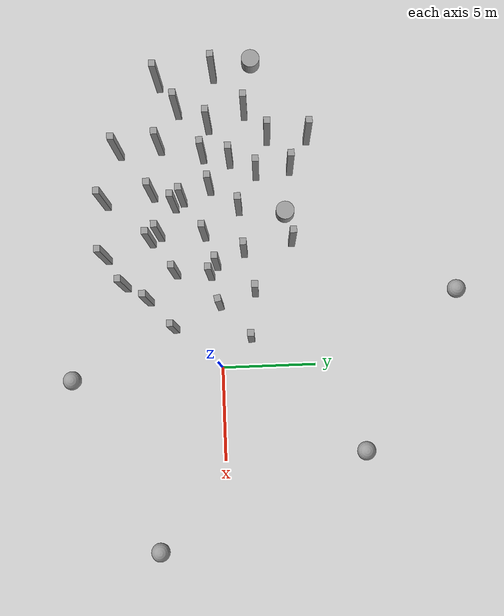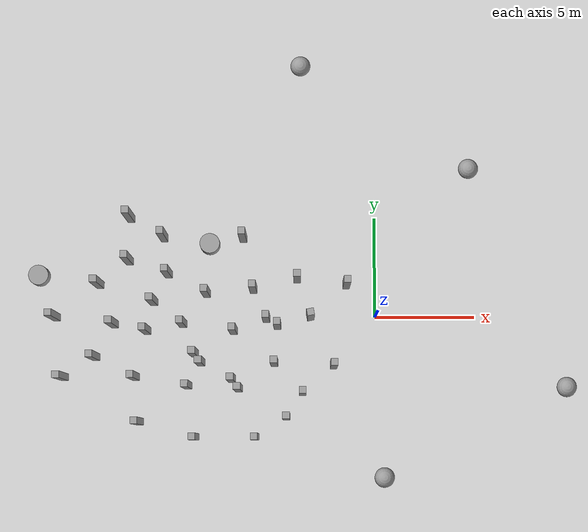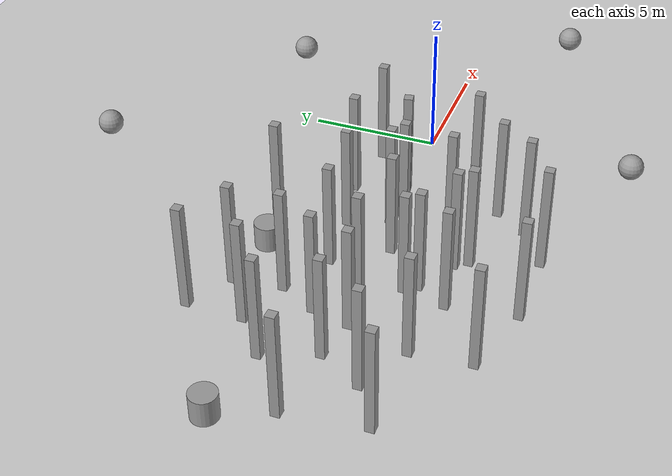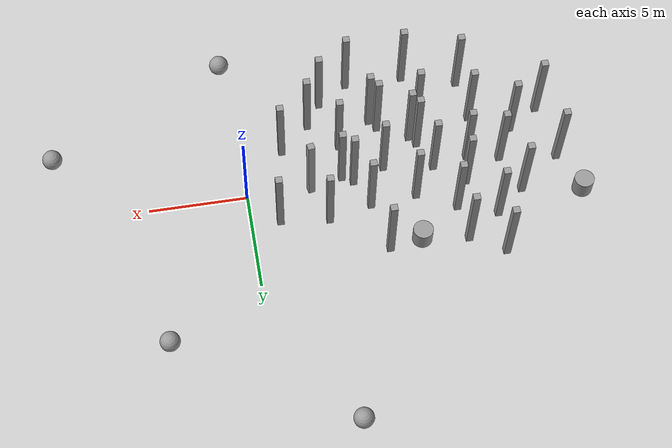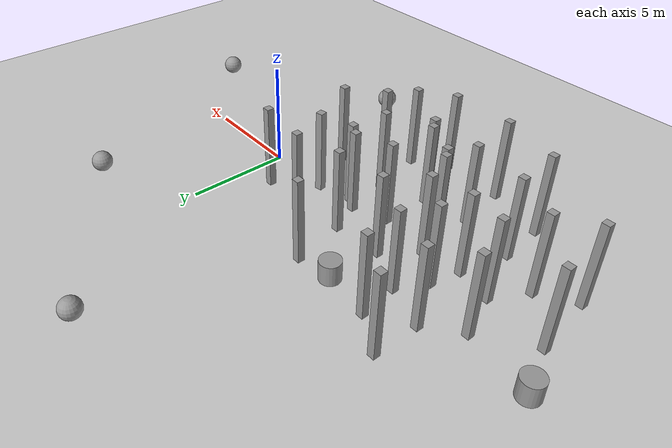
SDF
<sdf version="1.7">
 <world name="default">
  <light name="sun" type="directional">
   <pose>0 0 10 0 -0 0</pose>
   <diffuse>0.8 0.8 0.8 1</diffuse>
   <specular>0.2 0.2 0.2 1</specular>
   <attenuation>
    <range>1000</range>
    <constant>0.9</constant>
    <linear>0.01</linear>
    <quadratic>0.001</quadratic>
   </attenuation>
   <direction>-0.5 0.1 -0.9</direction>
   <spot><inner_angle>0</inner_angle><outer_angle>0</outer_angle><falloff>0</falloff></spot>
  </light>
  <model name="ground_plane">
   <static>1</static>
   <link name="link">
    <collision name="collision">
     <geometry><plane><normal>0 0 1</normal><size>100 100</size></plane></geometry>
     <surface>
      <contact><collide_bitmask>65535</collide_bitmask></contact>
      <friction><ode><mu>100</mu><mu2>50</mu2></ode></friction>
     </surface>
    </collision>
    <visual name="visual">
     <cast_shadows>0</cast_shadows>
     <geometry><plane><normal>0 0 1</normal><size>100 100</size></plane></geometry>
     <material>
      <script><uri>file://media/materials/scripts/gazebo.material</uri><name>Gazebo/Grey</name></script>
     </material>
    </visual>
   </link>
  </model>
  <gravity>0 0 -9.8</gravity>
  <magnetic_field>6e-06 2.3e-05 -4.2e-05</magnetic_field>
  <atmosphere type="adiabatic"/>
  <physics type="ode">
   <max_step_size>0.001</max_step_size>
   <real_time_factor>1</real_time_factor>
   <real_time_update_rate>1000</real_time_update_rate>
  </physics>
  <scene><ambient>0.4 0.4 0.4 1</ambient><background>0.7 0.7 0.7 1</background><shadows>1</shadows></scene>
  <spherical_coordinates>
   <surface_model>EARTH_WGS84</surface_model>
   <latitude_deg>0</latitude_deg>
   <longitude_deg>0</longitude_deg>
   <elevation>0</elevation>
   <heading_deg>0</heading_deg>
  </spherical_coordinates>
  <model name="unit_cylinder">
   <pose>-8.29376 3.67013 0.499992 -3e-06 2e-06 0</pose>
   <link name="link">
    <inertial>
     <mass>1</mass>
     <inertia><ixx>0.145833</ixx><ixy>0</ixy><ixz>0</ixz><iyy>0.145833</iyy><iyz>0</iyz><izz>0.125</izz></inertia>
    </inertial>
    <collision name="collision">
     <geometry><cylinder><radius>0.5</radius><length>1</length></cylinder></geometry>
    </collision>
    <visual name="visual">
     <geometry><cylinder><radius>0.5</radius><length>1</length></cylinder></geometry>
     <material>
      <script><name>Gazebo/Grey</name><uri>file://media/materials/scripts/gazebo.material</uri></script>
     </material>
    </visual>
   </link>
  </model>
  <model name="unit_sphere_2">
   <pose>4.71737 7.48223 0.5 0 -0 0</pose>
   <link name="link">
    <inertial>
     <mass>1</mass>
     <inertia><ixx>0.1</ixx><ixy>0</ixy><ixz>0</ixz><iyy>0.1</iyy><iyz>0</iyz><izz>0.1</izz></inertia>
    </inertial>
    <collision name="collision"><geometry><sphere><radius>0.5</radius></sphere></geometry></collision>
    <visual name="visual">
     <geometry><sphere><radius>0.5</radius></sphere></geometry>
     <material>
      <script><name>Gazebo/Grey</name><uri>file://media/materials/scripts/gazebo.material</uri></script>
     </material>
    </visual>
   </link>
  </model>
  <model name="unit_sphere_3">
   <pose>-3.74316 12.7332 0.5 0 -0 0</pose>
   <link name="link">
    <inertial>
     <mass>1</mass>
     <inertia><ixx>0.1</ixx><ixy>0</ixy><ixz>0</ixz><iyy>0.1</iyy><iyz>0</iyz><izz>0.1</izz></inertia>
    </inertial>
    <collision name="collision"><geometry><sphere><radius>0.5</radius></sphere></geometry></collision>
    <visual name="visual">
     <geometry><sphere><radius>0.5</radius></sphere></geometry>
     <material>
      <script><name>Gazebo/Grey</name><uri>file://media/materials/scripts/gazebo.material</uri></script>
     </material>
    </visual>
   </link>
  </model>
  <model name="unit_cylinder_1">
   <pose>-16.8605 2.08124 0.499996 4e-06 2e-06 -0</pose>
   <link name="link">
    <inertial>
     <mass>1</mass>
     <inertia><ixx>0.145833</ixx><ixy>0</ixy><ixz>0</ixz><iyy>0.145833</iyy><iyz>0</iyz><izz>0.125</izz></inertia>
    </inertial>
    <collision name="collision">
     <geometry><cylinder><radius>0.5</radius><length>1</length></cylinder></geometry>
    </collision>
    <visual name="visual">
     <geometry><cylinder><radius>0.5</radius><length>1</length></cylinder></geometry>
     <material>
      <script><name>Gazebo/Grey</name><uri>file://media/materials/scripts/gazebo.material</uri></script>
     </material>
    </visual>
   </link>
  </model>
  <model name="unit_sphere_4">
   <pose>9.57027 -3.52576 0.5 0 -0 0</pose>
   <link name="link">
    <inertial>
     <mass>1</mass>
     <inertia><ixx>0.1</ixx><ixy>0</ixy><ixz>0</ixz><iyy>0.1</iyy><iyz>0</iyz><izz>0.1</izz></inertia>
    </inertial>
    <collision name="collision"><geometry><sphere><radius>0.5</radius></sphere></geometry></collision>
    <visual name="visual">
     <geometry><sphere><radius>0.5</radius></sphere></geometry>
     <material>
      <script><name>Gazebo/Grey</name><uri>file://media/materials/scripts/gazebo.material</uri></script>
     </material>
    </visual>
   </link>
  </model>
  <model name="unit_sphere_5">
   <pose>0.446362 -8.02428 0.5 0 -0 0</pose>
   <link name="link">
    <inertial>
     <mass>1</mass>
     <inertia><ixx>0.1</ixx><ixy>0</ixy><ixz>0</ixz><iyy>0.1</iyy><iyz>0</iyz><izz>0.1</izz></inertia>
    </inertial>
    <collision name="collision"><geometry><sphere><radius>0.5</radius></sphere></geometry></collision>
    <visual name="visual">
     <geometry><sphere><radius>0.5</radius></sphere></geometry>
     <material>
      <script><name>Gazebo/Grey</name><uri>file://media/materials/scripts/gazebo.material</uri></script>
     </material>
    </visual>
   </link>
  </model>
  <light name="user_spot_light_0" type="spot">
   <pose>-15.8293 12.7519 1 0 -0 0</pose>
   <diffuse>0.5 0.5 0.5 1</diffuse>
   <specular>0.1 0.1 0.1 1</specular>
   <direction>0 0 -1</direction>
   <attenuation>
    <range>20</range>
    <constant>0.5</constant>
    <linear>0.01</linear>
    <quadratic>0.001</quadratic>
   </attenuation>
   <cast_shadows>0</cast_shadows>
   <spot><inner_angle>0.6</inner_angle><outer_angle>1</outer_angle><falloff>1</falloff></spot>
  </light>
  <light name="user_spot_light_1" type="spot">
   <pose>-0.982217 1.39334 1 0 -0 0</pose>
   <diffuse>0.5 0.5 0.5 1</diffuse>
   <specular>0.1 0.1 0.1 1</specular>
   <direction>0 0 -1</direction>
   <attenuation>
    <range>20</range>
    <constant>0.5</constant>
    <linear>0.01</linear>
    <quadratic>0.001</quadratic>
   </attenuation>
   <cast_shadows>0</cast_shadows>
   <spot><inner_angle>0.6</inner_angle><outer_angle>1</outer_angle><falloff>1</falloff></spot>
  </light>
  <model name="unit_box">
   <link name="link">
    <inertial>
     <mass>2.4304</mass>
     <inertia><ixx>3.54705</ixx><ixy>0</ixy><ixz>0</ixz><iyy>3.54798</iyy><iyz>0</iyz><izz>0.047215</izz></inertia>
    </inertial>
    <visual name="visual">
     <geometry><box><size>0.344761 0.338027 4.17123</size></box></geometry>
     <material>
      <script><name>Gazebo/Grey</name><uri>file://media/materials/scripts/gazebo.material</uri></script>
      <shader type="pixel"><normal_map>__default__</normal_map></shader>
      <ambient>0.3 0.3 0.3 1</ambient>
      <diffuse>0.7 0.7 0.7 1</diffuse>
      <specular>0.01 0.01 0.01 1</specular>
      <emissive>0 0 0 1</emissive>
     </material>
    </visual>
    <collision name="collision">
     <geometry><box><size>0.344761 0.338027 4.17123</size></box></geometry>
     <surface>
      <friction>
       <ode><mu>1</mu><mu2>1</mu2><fdir1>0 0 0</fdir1><slip1>0</slip1><slip2>0</slip2></ode>
       <torsional>
        <coefficient>1</coefficient>
        <patch_radius>0</patch_radius>
        <surface_radius>0</surface_radius>
        <use_patch_radius>1</use_patch_radius>
        <ode><slip>0</slip></ode>
       </torsional>
      </friction>
      <bounce><restitution_coefficient>0</restitution_coefficient><threshold>1e+06</threshold></bounce>
      <contact>
       <collide_without_contact>0</collide_without_contact>
       <collide_without_contact_bitmask>1</collide_without_contact_bitmask>
       <collide_bitmask>1</collide_bitmask>
       <ode>
        <soft_cfm>0</soft_cfm>
        <soft_erp>0.2</soft_erp>
        <kp>1e+13</kp>
        <kd>1</kd>
        <max_vel>0.01</max_vel>
        <min_depth>0</min_depth>
       </ode>
       <bullet>
        <split_impulse>1</split_impulse>
        <split_impulse_penetration_threshold>-0.01</split_impulse_penetration_threshold>
        <soft_cfm>0</soft_cfm>
        <soft_erp>0.2</soft_erp>
        <kp>1e+13</kp>
        <kd>1</kd>
       </bullet>
      </contact>
     </surface>
    </collision>
   </link>
   <static>0</static>
   <pose>-4.89873 -0.436914 2.08562 1e-06 -0 0.00158</pose>
  </model>
  <model name="unit_box_clone">
   <link name="link">
    <inertial>
     <mass>2.4304</mass>
     <inertia><ixx>3.54705</ixx><ixy>0</ixy><ixz>0</ixz><iyy>3.54798</iyy><iyz>0</iyz><izz>0.047215</izz></inertia>
    </inertial>
    <visual name="visual">
     <geometry><box><size>0.344761 0.338027 4.17123</size></box></geometry>
     <material>
      <script><name>Gazebo/Grey</name><uri>file://media/materials/scripts/gazebo.material</uri></script>
      <shader type="pixel"><normal_map>__default__</normal_map></shader>
      <ambient>0.3 0.3 0.3 1</ambient>
      <diffuse>0.7 0.7 0.7 1</diffuse>
      <specular>0.01 0.01 0.01 1</specular>
      <emissive>0 0 0 1</emissive>
     </material>
    </visual>
    <collision name="collision">
     <geometry><box><size>0.344761 0.338027 4.17123</size></box></geometry>
     <surface>
      <friction>
       <ode><mu>1</mu><mu2>1</mu2><fdir1>0 0 0</fdir1><slip1>0</slip1><slip2>0</slip2></ode>
       <torsional>
        <coefficient>1</coefficient>
        <patch_radius>0</patch_radius>
        <surface_radius>0</surface_radius>
        <use_patch_radius>1</use_patch_radius>
        <ode><slip>0</slip></ode>
       </torsional>
      </friction>
      <bounce><restitution_coefficient>0</restitution_coefficient><threshold>1e+06</threshold></bounce>
      <contact>
       <collide_without_contact>0</collide_without_contact>
       <collide_without_contact_bitmask>1</collide_without_contact_bitmask>
       <collide_bitmask>1</collide_bitmask>
       <ode>
        <soft_cfm>0</soft_cfm>
        <soft_erp>0.2</soft_erp>
        <kp>1e+13</kp>
        <kd>1</kd>
        <max_vel>0.01</max_vel>
        <min_depth>0</min_depth>
       </ode>
       <bullet>
        <split_impulse>1</split_impulse>
        <split_impulse_penetration_threshold>-0.01</split_impulse_penetration_threshold>
        <soft_cfm>0</soft_cfm>
        <soft_erp>0.2</soft_erp>
        <kp>1e+13</kp>
        <kd>1</kd>
       </bullet>
      </contact>
     </surface>
    </collision>
   </link>
   <static>0</static>
   <pose>-2.09348 -2.42381 2.08562 -1e-06 1.1e-05 0.001567</pose>
  </model>
  <model name="unit_box_clone_0">
   <link name="link">
    <inertial>
     <mass>2.4304</mass>
     <inertia><ixx>3.54705</ixx><ixy>0</ixy><ixz>0</ixz><iyy>3.54798</iyy><iyz>0</iyz><izz>0.047215</izz></inertia>
    </inertial>
    <visual name="visual">
     <geometry><box><size>0.344761 0.338027 4.17123</size></box></geometry>
     <material>
      <script><name>Gazebo/Grey</name><uri>file://media/materials/scripts/gazebo.material</uri></script>
      <shader type="pixel"><normal_map>__default__</normal_map></shader>
      <ambient>0.3 0.3 0.3 1</ambient>
      <diffuse>0.7 0.7 0.7 1</diffuse>
      <specular>0.01 0.01 0.01 1</specular>
      <emissive>0 0 0 1</emissive>
     </material>
    </visual>
    <collision name="collision">
     <geometry><box><size>0.344761 0.338027 4.17123</size></box></geometry>
     <surface>
      <friction>
       <ode><mu>1</mu><mu2>1</mu2><fdir1>0 0 0</fdir1><slip1>0</slip1><slip2>0</slip2></ode>
       <torsional>
        <coefficient>1</coefficient>
        <patch_radius>0</patch_radius>
        <surface_radius>0</surface_radius>
        <use_patch_radius>1</use_patch_radius>
        <ode><slip>0</slip></ode>
       </torsional>
      </friction>
      <bounce><restitution_coefficient>0</restitution_coefficient><threshold>1e+06</threshold></bounce>
      <contact>
       <collide_without_contact>0</collide_without_contact>
       <collide_without_contact_bitmask>1</collide_without_contact_bitmask>
       <collide_bitmask>1</collide_bitmask>
       <ode>
        <soft_cfm>0</soft_cfm>
        <soft_erp>0.2</soft_erp>
        <kp>1e+13</kp>
        <kd>1</kd>
        <max_vel>0.01</max_vel>
        <min_depth>0</min_depth>
       </ode>
       <bullet>
        <split_impulse>1</split_impulse>
        <split_impulse_penetration_threshold>-0.01</split_impulse_penetration_threshold>
        <soft_cfm>0</soft_cfm>
        <soft_erp>0.2</soft_erp>
        <kp>1e+13</kp>
        <kd>1</kd>
       </bullet>
      </contact>
     </surface>
    </collision>
   </link>
   <static>0</static>
   <pose>-1.45402 1.61345 2.08562 4e-06 -0 -0.00107</pose>
  </model>
  <model name="unit_box_clone_1">
   <link name="link">
    <inertial>
     <mass>2.4304</mass>
     <inertia><ixx>3.54705</ixx><ixy>0</ixy><ixz>0</ixz><iyy>3.54798</iyy><iyz>0</iyz><izz>0.047215</izz></inertia>
    </inertial>
    <visual name="visual">
     <geometry><box><size>0.344761 0.338027 4.17123</size></box></geometry>
     <material>
      <script><name>Gazebo/Grey</name><uri>file://media/materials/scripts/gazebo.material</uri></script>
      <shader type="pixel"><normal_map>__default__</normal_map></shader>
      <ambient>0.3 0.3 0.3 1</ambient>
      <diffuse>0.7 0.7 0.7 1</diffuse>
      <specular>0.01 0.01 0.01 1</specular>
      <emissive>0 0 0 1</emissive>
     </material>
    </visual>
    <collision name="collision">
     <geometry><box><size>0.344761 0.338027 4.17123</size></box></geometry>
     <surface>
      <friction>
       <ode><mu>1</mu><mu2>1</mu2><fdir1>0 0 0</fdir1><slip1>0</slip1><slip2>0</slip2></ode>
       <torsional>
        <coefficient>1</coefficient>
        <patch_radius>0</patch_radius>
        <surface_radius>0</surface_radius>
        <use_patch_radius>1</use_patch_radius>
        <ode><slip>0</slip></ode>
       </torsional>
      </friction>
      <bounce><restitution_coefficient>0</restitution_coefficient><threshold>1e+06</threshold></bounce>
      <contact>
       <collide_without_contact>0</collide_without_contact>
       <collide_without_contact_bitmask>1</collide_without_contact_bitmask>
       <collide_bitmask>1</collide_bitmask>
       <ode>
        <soft_cfm>0</soft_cfm>
        <soft_erp>0.2</soft_erp>
        <kp>1e+13</kp>
        <kd>1</kd>
        <max_vel>0.01</max_vel>
        <min_depth>0</min_depth>
       </ode>
       <bullet>
        <split_impulse>1</split_impulse>
        <split_impulse_penetration_threshold>-0.01</split_impulse_penetration_threshold>
        <soft_cfm>0</soft_cfm>
        <soft_erp>0.2</soft_erp>
        <kp>1e+13</kp>
        <kd>1</kd>
       </bullet>
      </contact>
     </surface>
    </collision>
   </link>
   <static>0</static>
   <pose>-3.9128 1.89997 2.08562 3e-06 5e-06 0.001417</pose>
  </model>
  <model name="unit_box_clone_2">
   <link name="link">
    <inertial>
     <mass>2.4304</mass>
     <inertia><ixx>3.54705</ixx><ixy>0</ixy><ixz>0</ixz><iyy>3.54798</iyy><iyz>0</iyz><izz>0.047215</izz></inertia>
    </inertial>
    <visual name="visual">
     <geometry><box><size>0.344761 0.338027 4.17123</size></box></geometry>
     <material>
      <script><name>Gazebo/Grey</name><uri>file://media/materials/scripts/gazebo.material</uri></script>
      <shader type="pixel"><normal_map>__default__</normal_map></shader>
      <ambient>0.3 0.3 0.3 1</ambient>
      <diffuse>0.7 0.7 0.7 1</diffuse>
      <specular>0.01 0.01 0.01 1</specular>
      <emissive>0 0 0 1</emissive>
     </material>
    </visual>
    <collision name="collision">
     <geometry><box><size>0.344761 0.338027 4.17123</size></box></geometry>
     <surface>
      <friction>
       <ode><mu>1</mu><mu2>1</mu2><fdir1>0 0 0</fdir1><slip1>0</slip1><slip2>0</slip2></ode>
       <torsional>
        <coefficient>1</coefficient>
        <patch_radius>0</patch_radius>
        <surface_radius>0</surface_radius>
        <use_patch_radius>1</use_patch_radius>
        <ode><slip>0</slip></ode>
       </torsional>
      </friction>
      <bounce><restitution_coefficient>0</restitution_coefficient><threshold>1e+06</threshold></bounce>
      <contact>
       <collide_without_contact>0</collide_without_contact>
       <collide_without_contact_bitmask>1</collide_without_contact_bitmask>
       <collide_bitmask>1</collide_bitmask>
       <ode>
        <soft_cfm>0</soft_cfm>
        <soft_erp>0.2</soft_erp>
        <kp>1e+13</kp>
        <kd>1</kd>
        <max_vel>0.01</max_vel>
        <min_depth>0</min_depth>
       </ode>
       <bullet>
        <split_impulse>1</split_impulse>
        <split_impulse_penetration_threshold>-0.01</split_impulse_penetration_threshold>
        <soft_cfm>0</soft_cfm>
        <soft_erp>0.2</soft_erp>
        <kp>1e+13</kp>
        <kd>1</kd>
       </bullet>
      </contact>
     </surface>
    </collision>
   </link>
   <static>0</static>
   <pose>-5.05173 -2.29484 2.08562 1e-06 -1e-06 -0.001395</pose>
  </model>
  <model name="unit_box_clone_3">
   <link name="link">
    <inertial>
     <mass>2.4304</mass>
     <inertia><ixx>3.54705</ixx><ixy>0</ixy><ixz>0</ixz><iyy>3.54798</iyy><iyz>0</iyz><izz>0.047215</izz></inertia>
    </inertial>
    <visual name="visual">
     <geometry><box><size>0.344761 0.338027 4.17123</size></box></geometry>
     <material>
      <script><name>Gazebo/Grey</name><uri>file://media/materials/scripts/gazebo.material</uri></script>
      <shader type="pixel"><normal_map>__default__</normal_map></shader>
      <ambient>0.3 0.3 0.3 1</ambient>
      <diffuse>0.7 0.7 0.7 1</diffuse>
      <specular>0.01 0.01 0.01 1</specular>
      <emissive>0 0 0 1</emissive>
     </material>
    </visual>
    <collision name="collision">
     <geometry><box><size>0.344761 0.338027 4.17123</size></box></geometry>
     <surface>
      <friction>
       <ode><mu>1</mu><mu2>1</mu2><fdir1>0 0 0</fdir1><slip1>0</slip1><slip2>0</slip2></ode>
       <torsional>
        <coefficient>1</coefficient>
        <patch_radius>0</patch_radius>
        <surface_radius>0</surface_radius>
        <use_patch_radius>1</use_patch_radius>
        <ode><slip>0</slip></ode>
       </torsional>
      </friction>
      <bounce><restitution_coefficient>0</restitution_coefficient><threshold>1e+06</threshold></bounce>
      <contact>
       <collide_without_contact>0</collide_without_contact>
       <collide_without_contact_bitmask>1</collide_without_contact_bitmask>
       <collide_bitmask>1</collide_bitmask>
       <ode>
        <soft_cfm>0</soft_cfm>
        <soft_erp>0.2</soft_erp>
        <kp>1e+13</kp>
        <kd>1</kd>
        <max_vel>0.01</max_vel>
        <min_depth>0</min_depth>
       </ode>
       <bullet>
        <split_impulse>1</split_impulse>
        <split_impulse_penetration_threshold>-0.01</split_impulse_penetration_threshold>
        <soft_cfm>0</soft_cfm>
        <soft_erp>0.2</soft_erp>
        <kp>1e+13</kp>
        <kd>1</kd>
       </bullet>
      </contact>
     </surface>
    </collision>
   </link>
   <static>0</static>
   <pose>-3.25519 0.006675 2.08562 -1e-06 -2e-06 0.18258</pose>
  </model>
  <model name="unit_box_clone_4">
   <link name="link">
    <inertial>
     <mass>2.4304</mass>
     <inertia><ixx>3.54705</ixx><ixy>0</ixy><ixz>0</ixz><iyy>3.54798</iyy><iyz>0</iyz><izz>0.047215</izz></inertia>
    </inertial>
    <visual name="visual">
     <geometry><box><size>0.344761 0.338027 4.17123</size></box></geometry>
     <material>
      <script><name>Gazebo/Grey</name><uri>file://media/materials/scripts/gazebo.material</uri></script>
      <shader type="pixel"><normal_map>__default__</normal_map></shader>
      <ambient>0.3 0.3 0.3 1</ambient>
      <diffuse>0.7 0.7 0.7 1</diffuse>
      <specular>0.01 0.01 0.01 1</specular>
      <emissive>0 0 0 1</emissive>
     </material>
    </visual>
    <collision name="collision">
     <geometry><box><size>0.344761 0.338027 4.17123</size></box></geometry>
     <surface>
      <friction>
       <ode><mu>1</mu><mu2>1</mu2><fdir1>0 0 0</fdir1><slip1>0</slip1><slip2>0</slip2></ode>
       <torsional>
        <coefficient>1</coefficient>
        <patch_radius>0</patch_radius>
        <surface_radius>0</surface_radius>
        <use_patch_radius>1</use_patch_radius>
        <ode><slip>0</slip></ode>
       </torsional>
      </friction>
      <bounce><restitution_coefficient>0</restitution_coefficient><threshold>1e+06</threshold></bounce>
      <contact>
       <collide_without_contact>0</collide_without_contact>
       <collide_without_contact_bitmask>1</collide_without_contact_bitmask>
       <collide_bitmask>1</collide_bitmask>
       <ode>
        <soft_cfm>0</soft_cfm>
        <soft_erp>0.2</soft_erp>
        <kp>1e+13</kp>
        <kd>1</kd>
        <max_vel>0.01</max_vel>
        <min_depth>0</min_depth>
       </ode>
       <bullet>
        <split_impulse>1</split_impulse>
        <split_impulse_penetration_threshold>-0.01</split_impulse_penetration_threshold>
        <soft_cfm>0</soft_cfm>
        <soft_erp>0.2</soft_erp>
        <kp>1e+13</kp>
        <kd>1</kd>
       </bullet>
      </contact>
     </surface>
    </collision>
   </link>
   <static>0</static>
   <pose>-3.63524 -3.77191 2.08563 2e-06 6.6e-05 0.001427</pose>
  </model>
  <model name="unit_box_clone_5">
   <link name="link">
    <inertial>
     <mass>2.4304</mass>
     <inertia><ixx>3.54705</ixx><ixy>0</ixy><ixz>0</ixz><iyy>3.54798</iyy><iyz>0</iyz><izz>0.047215</izz></inertia>
    </inertial>
    <visual name="visual">
     <geometry><box><size>0.344761 0.338027 4.17123</size></box></geometry>
     <material>
      <script><name>Gazebo/Grey</name><uri>file://media/materials/scripts/gazebo.material</uri></script>
      <shader type="pixel"><normal_map>__default__</normal_map></shader>
      <ambient>0.3 0.3 0.3 1</ambient>
      <diffuse>0.7 0.7 0.7 1</diffuse>
      <specular>0.01 0.01 0.01 1</specular>
      <emissive>0 0 0 1</emissive>
     </material>
    </visual>
    <collision name="collision">
     <geometry><box><size>0.344761 0.338027 4.17123</size></box></geometry>
     <surface>
      <friction>
       <ode><mu>1</mu><mu2>1</mu2><fdir1>0 0 0</fdir1><slip1>0</slip1><slip2>0</slip2></ode>
       <torsional>
        <coefficient>1</coefficient>
        <patch_radius>0</patch_radius>
        <surface_radius>0</surface_radius>
        <use_patch_radius>1</use_patch_radius>
        <ode><slip>0</slip></ode>
       </torsional>
      </friction>
      <bounce><restitution_coefficient>0</restitution_coefficient><threshold>1e+06</threshold></bounce>
      <contact>
       <collide_without_contact>0</collide_without_contact>
       <collide_without_contact_bitmask>1</collide_without_contact_bitmask>
       <collide_bitmask>1</collide_bitmask>
       <ode>
        <soft_cfm>0</soft_cfm>
        <soft_erp>0.2</soft_erp>
        <kp>1e+13</kp>
        <kd>1</kd>
        <max_vel>0.01</max_vel>
        <min_depth>0</min_depth>
       </ode>
       <bullet>
        <split_impulse>1</split_impulse>
        <split_impulse_penetration_threshold>-0.01</split_impulse_penetration_threshold>
        <soft_cfm>0</soft_cfm>
        <soft_erp>0.2</soft_erp>
        <kp>1e+13</kp>
        <kd>1</kd>
       </bullet>
      </contact>
     </surface>
    </collision>
   </link>
   <static>0</static>
   <pose>-6.09968 1.38347 2.08562 0 2e-06 0.003616</pose>
  </model>
  <model name="unit_box_clone_6">
   <link name="link">
    <inertial>
     <mass>2.4304</mass>
     <inertia><ixx>3.54705</ixx><ixy>0</ixy><ixz>0</ixz><iyy>3.54798</iyy><iyz>0</iyz><izz>0.047215</izz></inertia>
    </inertial>
    <visual name="visual">
     <geometry><box><size>0.344761 0.338027 4.17123</size></box></geometry>
     <material>
      <script><name>Gazebo/Grey</name><uri>file://media/materials/scripts/gazebo.material</uri></script>
      <shader type="pixel"><normal_map>__default__</normal_map></shader>
      <ambient>0.3 0.3 0.3 1</ambient>
      <diffuse>0.7 0.7 0.7 1</diffuse>
      <specular>0.01 0.01 0.01 1</specular>
      <emissive>0 0 0 1</emissive>
     </material>
    </visual>
    <collision name="collision">
     <geometry><box><size>0.344761 0.338027 4.17123</size></box></geometry>
     <surface>
      <friction>
       <ode><mu>1</mu><mu2>1</mu2><fdir1>0 0 0</fdir1><slip1>0</slip1><slip2>0</slip2></ode>
       <torsional>
        <coefficient>1</coefficient>
        <patch_radius>0</patch_radius>
        <surface_radius>0</surface_radius>
        <use_patch_radius>1</use_patch_radius>
        <ode><slip>0</slip></ode>
       </torsional>
      </friction>
      <bounce><restitution_coefficient>0</restitution_coefficient><threshold>1e+06</threshold></bounce>
      <contact>
       <collide_without_contact>0</collide_without_contact>
       <collide_without_contact_bitmask>1</collide_without_contact_bitmask>
       <collide_bitmask>1</collide_bitmask>
       <ode>
        <soft_cfm>0</soft_cfm>
        <soft_erp>0.2</soft_erp>
        <kp>1e+13</kp>
        <kd>1</kd>
        <max_vel>0.01</max_vel>
        <min_depth>0</min_depth>
       </ode>
       <bullet>
        <split_impulse>1</split_impulse>
        <split_impulse_penetration_threshold>-0.01</split_impulse_penetration_threshold>
        <soft_cfm>0</soft_cfm>
        <soft_erp>0.2</soft_erp>
        <kp>1e+13</kp>
        <kd>1</kd>
       </bullet>
      </contact>
     </surface>
    </collision>
   </link>
   <static>0</static>
   <pose>-7.08866 -0.698663 2.08562 -2e-06 -5e-06 0.001369</pose>
  </model>
  <model name="unit_box_clone_7">
   <link name="link">
    <inertial>
     <mass>2.4304</mass>
     <inertia><ixx>3.54705</ixx><ixy>0</ixy><ixz>0</ixz><iyy>3.54798</iyy><iyz>0</iyz><izz>0.047215</izz></inertia>
    </inertial>
    <visual name="visual">
     <geometry><box><size>0.344761 0.338027 4.17123</size></box></geometry>
     <material>
      <script><name>Gazebo/Grey</name><uri>file://media/materials/scripts/gazebo.material</uri></script>
      <shader type="pixel"><normal_map>__default__</normal_map></shader>
      <ambient>0.3 0.3 0.3 1</ambient>
      <diffuse>0.7 0.7 0.7 1</diffuse>
      <specular>0.01 0.01 0.01 1</specular>
      <emissive>0 0 0 1</emissive>
     </material>
    </visual>
    <collision name="collision">
     <geometry><box><size>0.344761 0.338027 4.17123</size></box></geometry>
     <surface>
      <friction>
       <ode><mu>1</mu><mu2>1</mu2><fdir1>0 0 0</fdir1><slip1>0</slip1><slip2>0</slip2></ode>
       <torsional>
        <coefficient>1</coefficient>
        <patch_radius>0</patch_radius>
        <surface_radius>0</surface_radius>
        <use_patch_radius>1</use_patch_radius>
        <ode><slip>0</slip></ode>
       </torsional>
      </friction>
      <bounce><restitution_coefficient>0</restitution_coefficient><threshold>1e+06</threshold></bounce>
      <contact>
       <collide_without_contact>0</collide_without_contact>
       <collide_without_contact_bitmask>1</collide_without_contact_bitmask>
       <collide_bitmask>1</collide_bitmask>
       <ode>
        <soft_cfm>0</soft_cfm>
        <soft_erp>0.2</soft_erp>
        <kp>1e+13</kp>
        <kd>1</kd>
        <max_vel>0.01</max_vel>
        <min_depth>0</min_depth>
       </ode>
       <bullet>
        <split_impulse>1</split_impulse>
        <split_impulse_penetration_threshold>-0.01</split_impulse_penetration_threshold>
        <soft_cfm>0</soft_cfm>
        <soft_erp>0.2</soft_erp>
        <kp>1e+13</kp>
        <kd>1</kd>
       </bullet>
      </contact>
     </surface>
    </collision>
   </link>
   <static>0</static>
   <pose>-7.16836 -3.10699 2.08562 -0 1e-05 -0.001384</pose>
  </model>
  <model name="unit_box_clone_8">
   <link name="link">
    <inertial>
     <mass>2.4304</mass>
     <inertia><ixx>3.54705</ixx><ixy>0</ixy><ixz>0</ixz><iyy>3.54798</iyy><iyz>0</iyz><izz>0.047215</izz></inertia>
    </inertial>
    <visual name="visual">
     <geometry><box><size>0.344761 0.338027 4.17123</size></box></geometry>
     <material>
      <script><name>Gazebo/Grey</name><uri>file://media/materials/scripts/gazebo.material</uri></script>
      <shader type="pixel"><normal_map>__default__</normal_map></shader>
      <ambient>0.3 0.3 0.3 1</ambient>
      <diffuse>0.7 0.7 0.7 1</diffuse>
      <specular>0.01 0.01 0.01 1</specular>
      <emissive>0 0 0 1</emissive>
     </material>
    </visual>
    <collision name="collision">
     <geometry><box><size>0.344761 0.338027 4.17123</size></box></geometry>
     <surface>
      <friction>
       <ode><mu>1</mu><mu2>1</mu2><fdir1>0 0 0</fdir1><slip1>0</slip1><slip2>0</slip2></ode>
       <torsional>
        <coefficient>1</coefficient>
        <patch_radius>0</patch_radius>
        <surface_radius>0</surface_radius>
        <use_patch_radius>1</use_patch_radius>
        <ode><slip>0</slip></ode>
       </torsional>
      </friction>
      <bounce><restitution_coefficient>0</restitution_coefficient><threshold>1e+06</threshold></bounce>
      <contact>
       <collide_without_contact>0</collide_without_contact>
       <collide_without_contact_bitmask>1</collide_without_contact_bitmask>
       <collide_bitmask>1</collide_bitmask>
       <ode>
        <soft_cfm>0</soft_cfm>
        <soft_erp>0.2</soft_erp>
        <kp>1e+13</kp>
        <kd>1</kd>
        <max_vel>0.01</max_vel>
        <min_depth>0</min_depth>
       </ode>
       <bullet>
        <split_impulse>1</split_impulse>
        <split_impulse_penetration_threshold>-0.01</split_impulse_penetration_threshold>
        <soft_cfm>0</soft_cfm>
        <soft_erp>0.2</soft_erp>
        <kp>1e+13</kp>
        <kd>1</kd>
       </bullet>
      </contact>
     </surface>
    </collision>
   </link>
   <static>0</static>
   <pose>-8.44398 1.17157 2.08562 0 8e-06 0.000473</pose>
  </model>
  <model name="unit_box_clone_9">
   <link name="link">
    <inertial>
     <mass>2.4304</mass>
     <inertia><ixx>3.54705</ixx><ixy>0</ixy><ixz>0</ixz><iyy>3.54798</iyy><iyz>0</iyz><izz>0.047215</izz></inertia>
    </inertial>
    <visual name="visual">
     <geometry><box><size>0.344761 0.338027 4.17123</size></box></geometry>
     <material>
      <script><name>Gazebo/Grey</name><uri>file://media/materials/scripts/gazebo.material</uri></script>
      <shader type="pixel"><normal_map>__default__</normal_map></shader>
      <ambient>0.3 0.3 0.3 1</ambient>
      <diffuse>0.7 0.7 0.7 1</diffuse>
      <specular>0.01 0.01 0.01 1</specular>
      <emissive>0 0 0 1</emissive>
     </material>
    </visual>
    <collision name="collision">
     <geometry><box><size>0.344761 0.338027 4.17123</size></box></geometry>
     <surface>
      <friction>
       <ode><mu>1</mu><mu2>1</mu2><fdir1>0 0 0</fdir1><slip1>0</slip1><slip2>0</slip2></ode>
       <torsional>
        <coefficient>1</coefficient>
        <patch_radius>0</patch_radius>
        <surface_radius>0</surface_radius>
        <use_patch_radius>1</use_patch_radius>
        <ode><slip>0</slip></ode>
       </torsional>
      </friction>
      <bounce><restitution_coefficient>0</restitution_coefficient><threshold>1e+06</threshold></bounce>
      <contact>
       <collide_without_contact>0</collide_without_contact>
       <collide_without_contact_bitmask>1</collide_without_contact_bitmask>
       <collide_bitmask>1</collide_bitmask>
       <ode>
        <soft_cfm>0</soft_cfm>
        <soft_erp>0.2</soft_erp>
        <kp>1e+13</kp>
        <kd>1</kd>
        <max_vel>0.01</max_vel>
        <min_depth>0</min_depth>
       </ode>
       <bullet>
        <split_impulse>1</split_impulse>
        <split_impulse_penetration_threshold>-0.01</split_impulse_penetration_threshold>
        <soft_cfm>0</soft_cfm>
        <soft_erp>0.2</soft_erp>
        <kp>1e+13</kp>
        <kd>1</kd>
       </bullet>
      </contact>
     </surface>
    </collision>
   </link>
   <static>0</static>
   <pose>-9.03364 -1.83112 2.08562 8e-06 2e-06 0.001634</pose>
  </model>
  <model name="unit_box_clone_10">
   <link name="link">
    <inertial>
     <mass>2.4304</mass>
     <inertia><ixx>3.54705</ixx><ixy>0</ixy><ixz>0</ixz><iyy>3.54798</iyy><iyz>0</iyz><izz>0.047215</izz></inertia>
    </inertial>
    <visual name="visual">
     <geometry><box><size>0.344761 0.338027 4.17123</size></box></geometry>
     <material>
      <script><name>Gazebo/Grey</name><uri>file://media/materials/scripts/gazebo.material</uri></script>
      <shader type="pixel"><normal_map>__default__</normal_map></shader>
      <ambient>0.3 0.3 0.3 1</ambient>
      <diffuse>0.7 0.7 0.7 1</diffuse>
      <specular>0.01 0.01 0.01 1</specular>
      <emissive>0 0 0 1</emissive>
     </material>
    </visual>
    <collision name="collision">
     <geometry><box><size>0.344761 0.338027 4.17123</size></box></geometry>
     <surface>
      <friction>
       <ode><mu>1</mu><mu2>1</mu2><fdir1>0 0 0</fdir1><slip1>0</slip1><slip2>0</slip2></ode>
       <torsional>
        <coefficient>1</coefficient>
        <patch_radius>0</patch_radius>
        <surface_radius>0</surface_radius>
        <use_patch_radius>1</use_patch_radius>
        <ode><slip>0</slip></ode>
       </torsional>
      </friction>
      <bounce><restitution_coefficient>0</restitution_coefficient><threshold>1e+06</threshold></bounce>
      <contact>
       <collide_without_contact>0</collide_without_contact>
       <collide_without_contact_bitmask>1</collide_without_contact_bitmask>
       <collide_bitmask>1</collide_bitmask>
       <ode>
        <soft_cfm>0</soft_cfm>
        <soft_erp>0.2</soft_erp>
        <kp>1e+13</kp>
        <kd>1</kd>
        <max_vel>0.01</max_vel>
        <min_depth>0</min_depth>
       </ode>
       <bullet>
        <split_impulse>1</split_impulse>
        <split_impulse_penetration_threshold>-0.01</split_impulse_penetration_threshold>
        <soft_cfm>0</soft_cfm>
        <soft_erp>0.2</soft_erp>
        <kp>1e+13</kp>
        <kd>1</kd>
       </bullet>
      </contact>
     </surface>
    </collision>
   </link>
   <static>0</static>
   <pose>-6.61939 3.96506 2.08562 0 -7e-06 -0.001889</pose>
  </model>
  <model name="unit_box_clone_11">
   <link name="link">
    <inertial>
     <mass>2.4304</mass>
     <inertia><ixx>3.54705</ixx><ixy>0</ixy><ixz>0</ixz><iyy>3.54798</iyy><iyz>0</iyz><izz>0.047215</izz></inertia>
    </inertial>
    <visual name="visual">
     <geometry><box><size>0.344761 0.338027 4.17123</size></box></geometry>
     <material>
      <script><name>Gazebo/Grey</name><uri>file://media/materials/scripts/gazebo.material</uri></script>
      <shader type="pixel"><normal_map>__default__</normal_map></shader>
      <ambient>0.3 0.3 0.3 1</ambient>
      <diffuse>0.7 0.7 0.7 1</diffuse>
      <specular>0.01 0.01 0.01 1</specular>
      <emissive>0 0 0 1</emissive>
     </material>
    </visual>
    <collision name="collision">
     <geometry><box><size>0.344761 0.338027 4.17123</size></box></geometry>
     <surface>
      <friction>
       <ode><mu>1</mu><mu2>1</mu2><fdir1>0 0 0</fdir1><slip1>0</slip1><slip2>0</slip2></ode>
       <torsional>
        <coefficient>1</coefficient>
        <patch_radius>0</patch_radius>
        <surface_radius>0</surface_radius>
        <use_patch_radius>1</use_patch_radius>
        <ode><slip>0</slip></ode>
       </torsional>
      </friction>
      <bounce><restitution_coefficient>0</restitution_coefficient><threshold>1e+06</threshold></bounce>
      <contact>
       <collide_without_contact>0</collide_without_contact>
       <collide_without_contact_bitmask>1</collide_without_contact_bitmask>
       <collide_bitmask>1</collide_bitmask>
       <ode>
        <soft_cfm>0</soft_cfm>
        <soft_erp>0.2</soft_erp>
        <kp>1e+13</kp>
        <kd>1</kd>
        <max_vel>0.01</max_vel>
        <min_depth>0</min_depth>
       </ode>
       <bullet>
        <split_impulse>1</split_impulse>
        <split_impulse_penetration_threshold>-0.01</split_impulse_penetration_threshold>
        <soft_cfm>0</soft_cfm>
        <soft_erp>0.2</soft_erp>
        <kp>1e+13</kp>
        <kd>1</kd>
       </bullet>
      </contact>
     </surface>
    </collision>
   </link>
   <static>0</static>
   <pose>-5.44967 -0.095249 2.08562 -1e-06 1.9e-05 0.001417</pose>
  </model>
  <model name="unit_box_clone_12">
   <link name="link">
    <inertial>
     <mass>2.4304</mass>
     <inertia><ixx>3.54705</ixx><ixy>0</ixy><ixz>0</ixz><iyy>3.54798</iyy><iyz>0</iyz><izz>0.047215</izz></inertia>
    </inertial>
    <visual name="visual">
     <geometry><box><size>0.344761 0.338027 4.17123</size></box></geometry>
     <material>
      <script><name>Gazebo/Grey</name><uri>file://media/materials/scripts/gazebo.material</uri></script>
      <shader type="pixel"><normal_map>__default__</normal_map></shader>
      <ambient>0.3 0.3 0.3 1</ambient>
      <diffuse>0.7 0.7 0.7 1</diffuse>
      <specular>0.01 0.01 0.01 1</specular>
      <emissive>0 0 0 1</emissive>
     </material>
    </visual>
    <collision name="collision">
     <geometry><box><size>0.344761 0.338027 4.17123</size></box></geometry>
     <surface>
      <friction>
       <ode><mu>1</mu><mu2>1</mu2><fdir1>0 0 0</fdir1><slip1>0</slip1><slip2>0</slip2></ode>
       <torsional>
        <coefficient>1</coefficient>
        <patch_radius>0</patch_radius>
        <surface_radius>0</surface_radius>
        <use_patch_radius>1</use_patch_radius>
        <ode><slip>0</slip></ode>
       </torsional>
      </friction>
      <bounce><restitution_coefficient>0</restitution_coefficient><threshold>1e+06</threshold></bounce>
      <contact>
       <collide_without_contact>0</collide_without_contact>
       <collide_without_contact_bitmask>1</collide_without_contact_bitmask>
       <collide_bitmask>1</collide_bitmask>
       <ode>
        <soft_cfm>0</soft_cfm>
        <soft_erp>0.2</soft_erp>
        <kp>1e+13</kp>
        <kd>1</kd>
        <max_vel>0.01</max_vel>
        <min_depth>0</min_depth>
       </ode>
       <bullet>
        <split_impulse>1</split_impulse>
        <split_impulse_penetration_threshold>-0.01</split_impulse_penetration_threshold>
        <soft_cfm>0</soft_cfm>
        <soft_erp>0.2</soft_erp>
        <kp>1e+13</kp>
        <kd>1</kd>
       </bullet>
      </contact>
     </surface>
    </collision>
   </link>
   <static>0</static>
   <pose>-8.71743 -2.2826 2.08562 0 -1e-06 0.001927</pose>
  </model>
  <model name="unit_box_clone_13">
   <link name="link">
    <inertial>
     <mass>2.4304</mass>
     <inertia><ixx>3.54705</ixx><ixy>0</ixy><ixz>0</ixz><iyy>3.54798</iyy><iyz>0</iyz><izz>0.047215</izz></inertia>
    </inertial>
    <visual name="visual">
     <geometry><box><size>0.344761 0.338027 4.17123</size></box></geometry>
     <material>
      <script><name>Gazebo/Grey</name><uri>file://media/materials/scripts/gazebo.material</uri></script>
      <shader type="pixel"><normal_map>__default__</normal_map></shader>
      <ambient>0.3 0.3 0.3 1</ambient>
      <diffuse>0.7 0.7 0.7 1</diffuse>
      <specular>0.01 0.01 0.01 1</specular>
      <emissive>0 0 0 1</emissive>
     </material>
    </visual>
    <collision name="collision">
     <geometry><box><size>0.344761 0.338027 4.17123</size></box></geometry>
     <surface>
      <friction>
       <ode><mu>1</mu><mu2>1</mu2><fdir1>0 0 0</fdir1><slip1>0</slip1><slip2>0</slip2></ode>
       <torsional>
        <coefficient>1</coefficient>
        <patch_radius>0</patch_radius>
        <surface_radius>0</surface_radius>
        <use_patch_radius>1</use_patch_radius>
        <ode><slip>0</slip></ode>
       </torsional>
      </friction>
      <bounce><restitution_coefficient>0</restitution_coefficient><threshold>1e+06</threshold></bounce>
      <contact>
       <collide_without_contact>0</collide_without_contact>
       <collide_without_contact_bitmask>1</collide_without_contact_bitmask>
       <collide_bitmask>1</collide_bitmask>
       <ode>
        <soft_cfm>0</soft_cfm>
        <soft_erp>0.2</soft_erp>
        <kp>1e+13</kp>
        <kd>1</kd>
        <max_vel>0.01</max_vel>
        <min_depth>0</min_depth>
       </ode>
       <bullet>
        <split_impulse>1</split_impulse>
        <split_impulse_penetration_threshold>-0.01</split_impulse_penetration_threshold>
        <soft_cfm>0</soft_cfm>
        <soft_erp>0.2</soft_erp>
        <kp>1e+13</kp>
        <kd>1</kd>
       </bullet>
      </contact>
     </surface>
    </collision>
   </link>
   <static>0</static>
   <pose>-6.83048 -3.57931 2.08562 -2e-06 -1e-06 0.000407</pose>
  </model>
  <model name="unit_box_clone_14">
   <link name="link">
    <inertial>
     <mass>2.4304</mass>
     <inertia><ixx>3.54705</ixx><ixy>0</ixy><ixz>0</ixz><iyy>3.54798</iyy><iyz>0</iyz><izz>0.047215</izz></inertia>
    </inertial>
    <visual name="visual">
     <geometry><box><size>0.344761 0.338027 4.17123</size></box></geometry>
     <material>
      <script><name>Gazebo/Grey</name><uri>file://media/materials/scripts/gazebo.material</uri></script>
      <shader type="pixel"><normal_map>__default__</normal_map></shader>
      <ambient>0.3 0.3 0.3 1</ambient>
      <diffuse>0.7 0.7 0.7 1</diffuse>
      <specular>0.01 0.01 0.01 1</specular>
      <emissive>0 0 0 1</emissive>
     </material>
    </visual>
    <collision name="collision">
     <geometry><box><size>0.344761 0.338027 4.17123</size></box></geometry>
     <surface>
      <friction>
       <ode><mu>1</mu><mu2>1</mu2><fdir1>0 0 0</fdir1><slip1>0</slip1><slip2>0</slip2></ode>
       <torsional>
        <coefficient>1</coefficient>
        <patch_radius>0</patch_radius>
        <surface_radius>0</surface_radius>
        <use_patch_radius>1</use_patch_radius>
        <ode><slip>0</slip></ode>
       </torsional>
      </friction>
      <bounce><restitution_coefficient>0</restitution_coefficient><threshold>1e+06</threshold></bounce>
      <contact>
       <collide_without_contact>0</collide_without_contact>
       <collide_without_contact_bitmask>1</collide_without_contact_bitmask>
       <collide_bitmask>1</collide_bitmask>
       <ode>
        <soft_cfm>0</soft_cfm>
        <soft_erp>0.2</soft_erp>
        <kp>1e+13</kp>
        <kd>1</kd>
        <max_vel>0.01</max_vel>
        <min_depth>0</min_depth>
       </ode>
       <bullet>
        <split_impulse>1</split_impulse>
        <split_impulse_penetration_threshold>-0.01</split_impulse_penetration_threshold>
        <soft_cfm>0</soft_cfm>
        <soft_erp>0.2</soft_erp>
        <kp>1e+13</kp>
        <kd>1</kd>
       </bullet>
      </contact>
     </surface>
    </collision>
   </link>
   <static>0</static>
   <pose>-9.62797 -0.350891 2.08562 1e-06 1e-06 0.002027</pose>
  </model>
  <model name="unit_box_clone_15">
   <link name="link">
    <inertial>
     <mass>2.4304</mass>
     <inertia><ixx>3.54705</ixx><ixy>0</ixy><ixz>0</ixz><iyy>3.54798</iyy><iyz>0</iyz><izz>0.047215</izz></inertia>
    </inertial>
    <visual name="visual">
     <geometry><box><size>0.344761 0.338027 4.17123</size></box></geometry>
     <material>
      <script><name>Gazebo/Grey</name><uri>file://media/materials/scripts/gazebo.material</uri></script>
      <shader type="pixel"><normal_map>__default__</normal_map></shader>
      <ambient>0.3 0.3 0.3 1</ambient>
      <diffuse>0.7 0.7 0.7 1</diffuse>
      <specular>0.01 0.01 0.01 1</specular>
      <emissive>0 0 0 1</emissive>
     </material>
    </visual>
    <collision name="collision">
     <geometry><box><size>0.344761 0.338027 4.17123</size></box></geometry>
     <surface>
      <friction>
       <ode><mu>1</mu><mu2>1</mu2><fdir1>0 0 0</fdir1><slip1>0</slip1><slip2>0</slip2></ode>
       <torsional>
        <coefficient>1</coefficient>
        <patch_radius>0</patch_radius>
        <surface_radius>0</surface_radius>
        <use_patch_radius>1</use_patch_radius>
        <ode><slip>0</slip></ode>
       </torsional>
      </friction>
      <bounce><restitution_coefficient>0</restitution_coefficient><threshold>1e+06</threshold></bounce>
      <contact>
       <collide_without_contact>0</collide_without_contact>
       <collide_without_contact_bitmask>1</collide_without_contact_bitmask>
       <collide_bitmask>1</collide_bitmask>
       <ode>
        <soft_cfm>0</soft_cfm>
        <soft_erp>0.2</soft_erp>
        <kp>1e+13</kp>
        <kd>1</kd>
        <max_vel>0.01</max_vel>
        <min_depth>0</min_depth>
       </ode>
       <bullet>
        <split_impulse>1</split_impulse>
        <split_impulse_penetration_threshold>-0.01</split_impulse_penetration_threshold>
        <soft_cfm>0</soft_cfm>
        <soft_erp>0.2</soft_erp>
        <kp>1e+13</kp>
        <kd>1</kd>
       </bullet>
      </contact>
     </surface>
    </collision>
   </link>
   <static>0</static>
   <pose>-10.3749 2.15662 2.08562 -4e-06 -4e-06 0.001895</pose>
  </model>
  <model name="unit_box_clone_16">
   <link name="link">
    <inertial>
     <mass>2.4304</mass>
     <inertia><ixx>3.54705</ixx><ixy>0</ixy><ixz>0</ixz><iyy>3.54798</iyy><iyz>0</iyz><izz>0.047215</izz></inertia>
    </inertial>
    <visual name="visual">
     <geometry><box><size>0.344761 0.338027 4.17123</size></box></geometry>
     <material>
      <script><name>Gazebo/Grey</name><uri>file://media/materials/scripts/gazebo.material</uri></script>
      <shader type="pixel"><normal_map>__default__</normal_map></shader>
      <ambient>0.3 0.3 0.3 1</ambient>
      <diffuse>0.7 0.7 0.7 1</diffuse>
      <specular>0.01 0.01 0.01 1</specular>
      <emissive>0 0 0 1</emissive>
     </material>
    </visual>
    <collision name="collision">
     <geometry><box><size>0.344761 0.338027 4.17123</size></box></geometry>
     <surface>
      <friction>
       <ode><mu>1</mu><mu2>1</mu2><fdir1>0 0 0</fdir1><slip1>0</slip1><slip2>0</slip2></ode>
       <torsional>
        <coefficient>1</coefficient>
        <patch_radius>0</patch_radius>
        <surface_radius>0</surface_radius>
        <use_patch_radius>1</use_patch_radius>
        <ode><slip>0</slip></ode>
       </torsional>
      </friction>
      <bounce><restitution_coefficient>0</restitution_coefficient><threshold>1e+06</threshold></bounce>
      <contact>
       <collide_without_contact>0</collide_without_contact>
       <collide_without_contact_bitmask>1</collide_without_contact_bitmask>
       <collide_bitmask>1</collide_bitmask>
       <ode>
        <soft_cfm>0</soft_cfm>
        <soft_erp>0.2</soft_erp>
        <kp>1e+13</kp>
        <kd>1</kd>
        <max_vel>0.01</max_vel>
        <min_depth>0</min_depth>
       </ode>
       <bullet>
        <split_impulse>1</split_impulse>
        <split_impulse_penetration_threshold>-0.01</split_impulse_penetration_threshold>
        <soft_cfm>0</soft_cfm>
        <soft_erp>0.2</soft_erp>
        <kp>1e+13</kp>
        <kd>1</kd>
       </bullet>
      </contact>
     </surface>
    </collision>
   </link>
   <static>0</static>
   <pose>-11.1024 0.762889 2.08562 -4e-06 -1e-06 -0.002996</pose>
  </model>
  <model name="unit_box_clone_17">
   <link name="link">
    <inertial>
     <mass>2.4304</mass>
     <inertia><ixx>3.54705</ixx><ixy>0</ixy><ixz>0</ixz><iyy>3.54798</iyy><iyz>0</iyz><izz>0.047215</izz></inertia>
    </inertial>
    <visual name="visual">
     <geometry><box><size>0.344761 0.338027 4.17123</size></box></geometry>
     <material>
      <script><name>Gazebo/Grey</name><uri>file://media/materials/scripts/gazebo.material</uri></script>
      <shader type="pixel"><normal_map>__default__</normal_map></shader>
      <ambient>0.3 0.3 0.3 1</ambient>
      <diffuse>0.7 0.7 0.7 1</diffuse>
      <specular>0.01 0.01 0.01 1</specular>
      <emissive>0 0 0 1</emissive>
     </material>
    </visual>
    <collision name="collision">
     <geometry><box><size>0.344761 0.338027 4.17123</size></box></geometry>
     <surface>
      <friction>
       <ode><mu>1</mu><mu2>1</mu2><fdir1>0 0 0</fdir1><slip1>0</slip1><slip2>0</slip2></ode>
       <torsional>
        <coefficient>1</coefficient>
        <patch_radius>0</patch_radius>
        <surface_radius>0</surface_radius>
        <use_patch_radius>1</use_patch_radius>
        <ode><slip>0</slip></ode>
       </torsional>
      </friction>
      <bounce><restitution_coefficient>0</restitution_coefficient><threshold>1e+06</threshold></bounce>
      <contact>
       <collide_without_contact>0</collide_without_contact>
       <collide_without_contact_bitmask>1</collide_without_contact_bitmask>
       <collide_bitmask>1</collide_bitmask>
       <ode>
        <soft_cfm>0</soft_cfm>
        <soft_erp>0.2</soft_erp>
        <kp>1e+13</kp>
        <kd>1</kd>
        <max_vel>0.01</max_vel>
        <min_depth>0</min_depth>
       </ode>
       <bullet>
        <split_impulse>1</split_impulse>
        <split_impulse_penetration_threshold>-0.01</split_impulse_penetration_threshold>
        <soft_cfm>0</soft_cfm>
        <soft_erp>0.2</soft_erp>
        <kp>1e+13</kp>
        <kd>1</kd>
       </bullet>
      </contact>
     </surface>
    </collision>
   </link>
   <static>0</static>
   <pose>-12 -2.99933 2.08562 1e-06 2e-06 0.002402</pose>
  </model>
  <model name="unit_box_clone_18">
   <link name="link">
    <inertial>
     <mass>2.4304</mass>
     <inertia><ixx>3.54705</ixx><ixy>0</ixy><ixz>0</ixz><iyy>3.54798</iyy><iyz>0</iyz><izz>0.047215</izz></inertia>
    </inertial>
    <visual name="visual">
     <geometry><box><size>0.344761 0.338027 4.17123</size></box></geometry>
     <material>
      <script><name>Gazebo/Grey</name><uri>file://media/materials/scripts/gazebo.material</uri></script>
      <shader type="pixel"><normal_map>__default__</normal_map></shader>
      <ambient>0.3 0.3 0.3 1</ambient>
      <diffuse>0.7 0.7 0.7 1</diffuse>
      <specular>0.01 0.01 0.01 1</specular>
      <emissive>0 0 0 1</emissive>
     </material>
    </visual>
    <collision name="collision">
     <geometry><box><size>0.344761 0.338027 4.17123</size></box></geometry>
     <surface>
      <friction>
       <ode><mu>1</mu><mu2>1</mu2><fdir1>0 0 0</fdir1><slip1>0</slip1><slip2>0</slip2></ode>
       <torsional>
        <coefficient>1</coefficient>
        <patch_radius>0</patch_radius>
        <surface_radius>0</surface_radius>
        <use_patch_radius>1</use_patch_radius>
        <ode><slip>0</slip></ode>
       </torsional>
      </friction>
      <bounce><restitution_coefficient>0</restitution_coefficient><threshold>1e+06</threshold></bounce>
      <contact>
       <collide_without_contact>0</collide_without_contact>
       <collide_without_contact_bitmask>1</collide_without_contact_bitmask>
       <collide_bitmask>1</collide_bitmask>
       <ode>
        <soft_cfm>0</soft_cfm>
        <soft_erp>0.2</soft_erp>
        <kp>1e+13</kp>
        <kd>1</kd>
        <max_vel>0.01</max_vel>
        <min_depth>0</min_depth>
       </ode>
       <bullet>
        <split_impulse>1</split_impulse>
        <split_impulse_penetration_threshold>-0.01</split_impulse_penetration_threshold>
        <soft_cfm>0</soft_cfm>
        <soft_erp>0.2</soft_erp>
        <kp>1e+13</kp>
        <kd>1</kd>
       </bullet>
      </contact>
     </surface>
    </collision>
   </link>
   <static>0</static>
   <pose>-11.4364 -0.684501 2.08562 0 -4.8e-05 -0.003025</pose>
  </model>
  <model name="unit_box_clone_19">
   <link name="link">
    <inertial>
     <mass>2.4304</mass>
     <inertia><ixx>3.54705</ixx><ixy>0</ixy><ixz>0</ixz><iyy>3.54798</iyy><iyz>0</iyz><izz>0.047215</izz></inertia>
    </inertial>
    <visual name="visual">
     <geometry><box><size>0.344761 0.338027 4.17123</size></box></geometry>
     <material>
      <script><name>Gazebo/Grey</name><uri>file://media/materials/scripts/gazebo.material</uri></script>
      <shader type="pixel"><normal_map>__default__</normal_map></shader>
      <ambient>0.3 0.3 0.3 1</ambient>
      <diffuse>0.7 0.7 0.7 1</diffuse>
      <specular>0.01 0.01 0.01 1</specular>
      <emissive>0 0 0 1</emissive>
     </material>
    </visual>
    <collision name="collision">
     <geometry><box><size>0.344761 0.338027 4.17123</size></box></geometry>
     <surface>
      <friction>
       <ode><mu>1</mu><mu2>1</mu2><fdir1>0 0 0</fdir1><slip1>0</slip1><slip2>0</slip2></ode>
       <torsional>
        <coefficient>1</coefficient>
        <patch_radius>0</patch_radius>
        <surface_radius>0</surface_radius>
        <use_patch_radius>1</use_patch_radius>
        <ode><slip>0</slip></ode>
       </torsional>
      </friction>
      <bounce><restitution_coefficient>0</restitution_coefficient><threshold>1e+06</threshold></bounce>
      <contact>
       <collide_without_contact>0</collide_without_contact>
       <collide_without_contact_bitmask>1</collide_without_contact_bitmask>
       <collide_bitmask>1</collide_bitmask>
       <ode>
        <soft_cfm>0</soft_cfm>
        <soft_erp>0.2</soft_erp>
        <kp>1e+13</kp>
        <kd>1</kd>
        <max_vel>0.01</max_vel>
        <min_depth>0</min_depth>
       </ode>
       <bullet>
        <split_impulse>1</split_impulse>
        <split_impulse_penetration_threshold>-0.01</split_impulse_penetration_threshold>
        <soft_cfm>0</soft_cfm>
        <soft_erp>0.2</soft_erp>
        <kp>1e+13</kp>
        <kd>1</kd>
       </bullet>
      </contact>
     </surface>
    </collision>
   </link>
   <static>0</static>
   <pose>-13.8179 1.63016 2.08562 -1e-06 1.1e-05 0.001608</pose>
  </model>
  <model name="unit_box_clone_20">
   <link name="link">
    <inertial>
     <mass>2.4304</mass>
     <inertia><ixx>3.54705</ixx><ixy>0</ixy><ixz>0</ixz><iyy>3.54798</iyy><iyz>0</iyz><izz>0.047215</izz></inertia>
    </inertial>
    <visual name="visual">
     <geometry><box><size>0.344761 0.338027 4.17123</size></box></geometry>
     <material>
      <script><name>Gazebo/Grey</name><uri>file://media/materials/scripts/gazebo.material</uri></script>
      <shader type="pixel"><normal_map>__default__</normal_map></shader>
      <ambient>0.3 0.3 0.3 1</ambient>
      <diffuse>0.7 0.7 0.7 1</diffuse>
      <specular>0.01 0.01 0.01 1</specular>
      <emissive>0 0 0 1</emissive>
     </material>
    </visual>
    <collision name="collision">
     <geometry><box><size>0.344761 0.338027 4.17123</size></box></geometry>
     <surface>
      <friction>
       <ode><mu>1</mu><mu2>1</mu2><fdir1>0 0 0</fdir1><slip1>0</slip1><slip2>0</slip2></ode>
       <torsional>
        <coefficient>1</coefficient>
        <patch_radius>0</patch_radius>
        <surface_radius>0</surface_radius>
        <use_patch_radius>1</use_patch_radius>
        <ode><slip>0</slip></ode>
       </torsional>
      </friction>
      <bounce><restitution_coefficient>0</restitution_coefficient><threshold>1e+06</threshold></bounce>
      <contact>
       <collide_without_contact>0</collide_without_contact>
       <collide_without_contact_bitmask>1</collide_without_contact_bitmask>
       <collide_bitmask>1</collide_bitmask>
       <ode>
        <soft_cfm>0</soft_cfm>
        <soft_erp>0.2</soft_erp>
        <kp>1e+13</kp>
        <kd>1</kd>
        <max_vel>0.01</max_vel>
        <min_depth>0</min_depth>
       </ode>
       <bullet>
        <split_impulse>1</split_impulse>
        <split_impulse_penetration_threshold>-0.01</split_impulse_penetration_threshold>
        <soft_cfm>0</soft_cfm>
        <soft_erp>0.2</soft_erp>
        <kp>1e+13</kp>
        <kd>1</kd>
       </bullet>
      </contact>
     </surface>
    </collision>
   </link>
   <static>0</static>
   <pose>-9.36759 -3.44244 2.08562 2e-06 -1.6e-05 0.001913</pose>
  </model>
  <model name="unit_box_clone_21">
   <link name="link">
    <inertial>
     <mass>2.4304</mass>
     <inertia><ixx>3.54705</ixx><ixy>0</ixy><ixz>0</ixz><iyy>3.54798</iyy><iyz>0</iyz><izz>0.047215</izz></inertia>
    </inertial>
    <visual name="visual">
     <geometry><box><size>0.344761 0.338027 4.17123</size></box></geometry>
     <material>
      <script><name>Gazebo/Grey</name><uri>file://media/materials/scripts/gazebo.material</uri></script>
      <shader type="pixel"><normal_map>__default__</normal_map></shader>
      <ambient>0.3 0.3 0.3 1</ambient>
      <diffuse>0.7 0.7 0.7 1</diffuse>
      <specular>0.01 0.01 0.01 1</specular>
      <emissive>0 0 0 1</emissive>
     </material>
    </visual>
    <collision name="collision">
     <geometry><box><size>0.344761 0.338027 4.17123</size></box></geometry>
     <surface>
      <friction>
       <ode><mu>1</mu><mu2>1</mu2><fdir1>0 0 0</fdir1><slip1>0</slip1><slip2>0</slip2></ode>
       <torsional>
        <coefficient>1</coefficient>
        <patch_radius>0</patch_radius>
        <surface_radius>0</surface_radius>
        <use_patch_radius>1</use_patch_radius>
        <ode><slip>0</slip></ode>
       </torsional>
      </friction>
      <bounce><restitution_coefficient>0</restitution_coefficient><threshold>1e+06</threshold></bounce>
      <contact>
       <collide_without_contact>0</collide_without_contact>
       <collide_without_contact_bitmask>1</collide_without_contact_bitmask>
       <collide_bitmask>1</collide_bitmask>
       <ode>
        <soft_cfm>0</soft_cfm>
        <soft_erp>0.2</soft_erp>
        <kp>1e+13</kp>
        <kd>1</kd>
        <max_vel>0.01</max_vel>
        <min_depth>0</min_depth>
       </ode>
       <bullet>
        <split_impulse>1</split_impulse>
        <split_impulse_penetration_threshold>-0.01</split_impulse_penetration_threshold>
        <soft_cfm>0</soft_cfm>
        <soft_erp>0.2</soft_erp>
        <kp>1e+13</kp>
        <kd>1</kd>
       </bullet>
      </contact>
     </surface>
    </collision>
   </link>
   <static>0</static>
   <pose>-13.0782 -0.350779 2.08562 1e-06 -0 0.001185</pose>
  </model>
  <model name="unit_box_clone_22">
   <link name="link">
    <inertial>
     <mass>2.4304</mass>
     <inertia><ixx>3.54705</ixx><ixy>0</ixy><ixz>0</ixz><iyy>3.54798</iyy><iyz>0</iyz><izz>0.047215</izz></inertia>
    </inertial>
    <visual name="visual">
     <geometry><box><size>0.344761 0.338027 4.17123</size></box></geometry>
     <material>
      <script><name>Gazebo/Grey</name><uri>file://media/materials/scripts/gazebo.material</uri></script>
      <shader type="pixel"><normal_map>__default__</normal_map></shader>
      <ambient>0.3 0.3 0.3 1</ambient>
      <diffuse>0.7 0.7 0.7 1</diffuse>
      <specular>0.01 0.01 0.01 1</specular>
      <emissive>0 0 0 1</emissive>
     </material>
    </visual>
    <collision name="collision">
     <geometry><box><size>0.344761 0.338027 4.17123</size></box></geometry>
     <surface>
      <friction>
       <ode><mu>1</mu><mu2>1</mu2><fdir1>0 0 0</fdir1><slip1>0</slip1><slip2>0</slip2></ode>
       <torsional>
        <coefficient>1</coefficient>
        <patch_radius>0</patch_radius>
        <surface_radius>0</surface_radius>
        <use_patch_radius>1</use_patch_radius>
        <ode><slip>0</slip></ode>
       </torsional>
      </friction>
      <bounce><restitution_coefficient>0</restitution_coefficient><threshold>1e+06</threshold></bounce>
      <contact>
       <collide_without_contact>0</collide_without_contact>
       <collide_without_contact_bitmask>1</collide_without_contact_bitmask>
       <collide_bitmask>1</collide_bitmask>
       <ode>
        <soft_cfm>0</soft_cfm>
        <soft_erp>0.2</soft_erp>
        <kp>1e+13</kp>
        <kd>1</kd>
        <max_vel>0.01</max_vel>
        <min_depth>0</min_depth>
       </ode>
       <bullet>
        <split_impulse>1</split_impulse>
        <split_impulse_penetration_threshold>-0.01</split_impulse_penetration_threshold>
        <soft_cfm>0</soft_cfm>
        <soft_erp>0.2</soft_erp>
        <kp>1e+13</kp>
        <kd>1</kd>
       </bullet>
      </contact>
     </surface>
    </collision>
   </link>
   <static>0</static>
   <pose>-8.99964 -5.99953 2.08562 0 2e-06 0.000211</pose>
  </model>
  <model name="unit_box_clone_23">
   <link name="link">
    <inertial>
     <mass>2.4304</mass>
     <inertia><ixx>3.54705</ixx><ixy>0</ixy><ixz>0</ixz><iyy>3.54798</iyy><iyz>0</iyz><izz>0.047215</izz></inertia>
    </inertial>
    <visual name="visual">
     <geometry><box><size>0.344761 0.338027 4.17123</size></box></geometry>
     <material>
      <script><name>Gazebo/Grey</name><uri>file://media/materials/scripts/gazebo.material</uri></script>
      <shader type="pixel"><normal_map>__default__</normal_map></shader>
      <ambient>0.3 0.3 0.3 1</ambient>
      <diffuse>0.7 0.7 0.7 1</diffuse>
      <specular>0.01 0.01 0.01 1</specular>
      <emissive>0 0 0 1</emissive>
     </material>
    </visual>
    <collision name="collision">
     <geometry><box><size>0.344761 0.338027 4.17123</size></box></geometry>
     <surface>
      <friction>
       <ode><mu>1</mu><mu2>1</mu2><fdir1>0 0 0</fdir1><slip1>0</slip1><slip2>0</slip2></ode>
       <torsional>
        <coefficient>1</coefficient>
        <patch_radius>0</patch_radius>
        <surface_radius>0</surface_radius>
        <use_patch_radius>1</use_patch_radius>
        <ode><slip>0</slip></ode>
       </torsional>
      </friction>
      <bounce><restitution_coefficient>0</restitution_coefficient><threshold>1e+06</threshold></bounce>
      <contact>
       <collide_without_contact>0</collide_without_contact>
       <collide_without_contact_bitmask>1</collide_without_contact_bitmask>
       <collide_bitmask>1</collide_bitmask>
       <ode>
        <soft_cfm>0</soft_cfm>
        <soft_erp>0.2</soft_erp>
        <kp>1e+13</kp>
        <kd>1</kd>
        <max_vel>0.01</max_vel>
        <min_depth>0</min_depth>
       </ode>
       <bullet>
        <split_impulse>1</split_impulse>
        <split_impulse_penetration_threshold>-0.01</split_impulse_penetration_threshold>
        <soft_cfm>0</soft_cfm>
        <soft_erp>0.2</soft_erp>
        <kp>1e+13</kp>
        <kd>1</kd>
       </bullet>
      </contact>
     </surface>
    </collision>
   </link>
   <static>0</static>
   <pose>-4.4447 -4.99945 2.08562 0 -0 0.001461</pose>
  </model>
  <model name="unit_box_clone_24">
   <link name="link">
    <inertial>
     <mass>2.4304</mass>
     <inertia><ixx>3.54705</ixx><ixy>0</ixy><ixz>0</ixz><iyy>3.54798</iyy><iyz>0</iyz><izz>0.047215</izz></inertia>
    </inertial>
    <visual name="visual">
     <geometry><box><size>0.344761 0.338027 4.17123</size></box></geometry>
     <material>
      <script><name>Gazebo/Grey</name><uri>file://media/materials/scripts/gazebo.material</uri></script>
      <shader type="pixel"><normal_map>__default__</normal_map></shader>
      <ambient>0.3 0.3 0.3 1</ambient>
      <diffuse>0.7 0.7 0.7 1</diffuse>
      <specular>0.01 0.01 0.01 1</specular>
      <emissive>0 0 0 1</emissive>
     </material>
    </visual>
    <collision name="collision">
     <geometry><box><size>0.344761 0.338027 4.17123</size></box></geometry>
     <surface>
      <friction>
       <ode><mu>1</mu><mu2>1</mu2><fdir1>0 0 0</fdir1><slip1>0</slip1><slip2>0</slip2></ode>
       <torsional>
        <coefficient>1</coefficient>
        <patch_radius>0</patch_radius>
        <surface_radius>0</surface_radius>
        <use_patch_radius>1</use_patch_radius>
        <ode><slip>0</slip></ode>
       </torsional>
      </friction>
      <bounce><restitution_coefficient>0</restitution_coefficient><threshold>1e+06</threshold></bounce>
      <contact>
       <collide_without_contact>0</collide_without_contact>
       <collide_without_contact_bitmask>1</collide_without_contact_bitmask>
       <collide_bitmask>1</collide_bitmask>
       <ode>
        <soft_cfm>0</soft_cfm>
        <soft_erp>0.2</soft_erp>
        <kp>1e+13</kp>
        <kd>1</kd>
        <max_vel>0.01</max_vel>
        <min_depth>0</min_depth>
       </ode>
       <bullet>
        <split_impulse>1</split_impulse>
        <split_impulse_penetration_threshold>-0.01</split_impulse_penetration_threshold>
        <soft_cfm>0</soft_cfm>
        <soft_erp>0.2</soft_erp>
        <kp>1e+13</kp>
        <kd>1</kd>
       </bullet>
      </contact>
     </surface>
    </collision>
   </link>
   <static>0</static>
   <pose>-5.99993 -5.99959 2.08562 -1.1e-05 -0 0.000827</pose>
  </model>
  <model name="unit_box_clone_25">
   <link name="link">
    <inertial>
     <mass>2.4304</mass>
     <inertia><ixx>3.54705</ixx><ixy>0</ixy><ixz>0</ixz><iyy>3.54798</iyy><iyz>0</iyz><izz>0.047215</izz></inertia>
    </inertial>
    <visual name="visual">
     <geometry><box><size>0.344761 0.338027 4.17123</size></box></geometry>
     <material>
      <script><name>Gazebo/Grey</name><uri>file://media/materials/scripts/gazebo.material</uri></script>
      <shader type="pixel"><normal_map>__default__</normal_map></shader>
      <ambient>0.3 0.3 0.3 1</ambient>
      <diffuse>0.7 0.7 0.7 1</diffuse>
      <specular>0.01 0.01 0.01 1</specular>
      <emissive>0 0 0 1</emissive>
     </material>
    </visual>
    <collision name="collision">
     <geometry><box><size>0.344761 0.338027 4.17123</size></box></geometry>
     <surface>
      <friction>
       <ode><mu>1</mu><mu2>1</mu2><fdir1>0 0 0</fdir1><slip1>0</slip1><slip2>0</slip2></ode>
       <torsional>
        <coefficient>1</coefficient>
        <patch_radius>0</patch_radius>
        <surface_radius>0</surface_radius>
        <use_patch_radius>1</use_patch_radius>
        <ode><slip>0</slip></ode>
       </torsional>
      </friction>
      <bounce><restitution_coefficient>0</restitution_coefficient><threshold>1e+06</threshold></bounce>
      <contact>
       <collide_without_contact>0</collide_without_contact>
       <collide_without_contact_bitmask>1</collide_without_contact_bitmask>
       <collide_bitmask>1</collide_bitmask>
       <ode>
        <soft_cfm>0</soft_cfm>
        <soft_erp>0.2</soft_erp>
        <kp>1e+13</kp>
        <kd>1</kd>
        <max_vel>0.01</max_vel>
        <min_depth>0</min_depth>
       </ode>
       <bullet>
        <split_impulse>1</split_impulse>
        <split_impulse_penetration_threshold>-0.01</split_impulse_penetration_threshold>
        <soft_cfm>0</soft_cfm>
        <soft_erp>0.2</soft_erp>
        <kp>1e+13</kp>
        <kd>1</kd>
       </bullet>
      </contact>
     </surface>
    </collision>
   </link>
   <static>0</static>
   <pose>-11.7975 -5.22673 2.08562 -1.6e-05 -3e-06 0.002424</pose>
  </model>
  <model name="unit_box_clone_26">
   <link name="link">
    <inertial>
     <mass>2.4304</mass>
     <inertia><ixx>3.54705</ixx><ixy>0</ixy><ixz>0</ixz><iyy>3.54798</iyy><iyz>0</iyz><izz>0.047215</izz></inertia>
    </inertial>
    <visual name="visual">
     <geometry><box><size>0.344761 0.338027 4.17123</size></box></geometry>
     <material>
      <script><name>Gazebo/Grey</name><uri>file://media/materials/scripts/gazebo.material</uri></script>
      <shader type="pixel"><normal_map>__default__</normal_map></shader>
      <ambient>0.3 0.3 0.3 1</ambient>
      <diffuse>0.7 0.7 0.7 1</diffuse>
      <specular>0.01 0.01 0.01 1</specular>
      <emissive>0 0 0 1</emissive>
     </material>
    </visual>
    <collision name="collision">
     <geometry><box><size>0.344761 0.338027 4.17123</size></box></geometry>
     <surface>
      <friction>
       <ode><mu>1</mu><mu2>1</mu2><fdir1>0 0 0</fdir1><slip1>0</slip1><slip2>0</slip2></ode>
       <torsional>
        <coefficient>1</coefficient>
        <patch_radius>0</patch_radius>
        <surface_radius>0</surface_radius>
        <use_patch_radius>1</use_patch_radius>
        <ode><slip>0</slip></ode>
       </torsional>
      </friction>
      <bounce><restitution_coefficient>0</restitution_coefficient><threshold>1e+06</threshold></bounce>
      <contact>
       <collide_without_contact>0</collide_without_contact>
       <collide_without_contact_bitmask>1</collide_without_contact_bitmask>
       <collide_bitmask>1</collide_bitmask>
       <ode>
        <soft_cfm>0</soft_cfm>
        <soft_erp>0.2</soft_erp>
        <kp>1e+13</kp>
        <kd>1</kd>
        <max_vel>0.01</max_vel>
        <min_depth>0</min_depth>
       </ode>
       <bullet>
        <split_impulse>1</split_impulse>
        <split_impulse_penetration_threshold>-0.01</split_impulse_penetration_threshold>
        <soft_cfm>0</soft_cfm>
        <soft_erp>0.2</soft_erp>
        <kp>1e+13</kp>
        <kd>1</kd>
       </bullet>
      </contact>
     </surface>
    </collision>
   </link>
   <static>0</static>
   <pose>-12.2945 4.99256 2.08562 3e-06 -0 0.002808</pose>
  </model>
  <model name="unit_box_clone_27">
   <link name="link">
    <inertial>
     <mass>2.4304</mass>
     <inertia><ixx>3.54705</ixx><ixy>0</ixy><ixz>0</ixz><iyy>3.54798</iyy><iyz>0</iyz><izz>0.047215</izz></inertia>
    </inertial>
    <visual name="visual">
     <geometry><box><size>0.344761 0.338027 4.17123</size></box></geometry>
     <material>
      <script><name>Gazebo/Grey</name><uri>file://media/materials/scripts/gazebo.material</uri></script>
      <shader type="pixel"><normal_map>__default__</normal_map></shader>
      <ambient>0.3 0.3 0.3 1</ambient>
      <diffuse>0.7 0.7 0.7 1</diffuse>
      <specular>0.01 0.01 0.01 1</specular>
      <emissive>0 0 0 1</emissive>
     </material>
    </visual>
    <collision name="collision">
     <geometry><box><size>0.344761 0.338027 4.17123</size></box></geometry>
     <surface>
      <friction>
       <ode><mu>1</mu><mu2>1</mu2><fdir1>0 0 0</fdir1><slip1>0</slip1><slip2>0</slip2></ode>
       <torsional>
        <coefficient>1</coefficient>
        <patch_radius>0</patch_radius>
        <surface_radius>0</surface_radius>
        <use_patch_radius>1</use_patch_radius>
        <ode><slip>0</slip></ode>
       </torsional>
      </friction>
      <bounce><restitution_coefficient>0</restitution_coefficient><threshold>1e+06</threshold></bounce>
      <contact>
       <collide_without_contact>0</collide_without_contact>
       <collide_without_contact_bitmask>1</collide_without_contact_bitmask>
       <collide_bitmask>1</collide_bitmask>
       <ode>
        <soft_cfm>0</soft_cfm>
        <soft_erp>0.2</soft_erp>
        <kp>1e+13</kp>
        <kd>1</kd>
        <max_vel>0.01</max_vel>
        <min_depth>0</min_depth>
       </ode>
       <bullet>
        <split_impulse>1</split_impulse>
        <split_impulse_penetration_threshold>-0.01</split_impulse_penetration_threshold>
        <soft_cfm>0</soft_cfm>
        <soft_erp>0.2</soft_erp>
        <kp>1e+13</kp>
        <kd>1</kd>
       </bullet>
      </contact>
     </surface>
    </collision>
   </link>
   <static>0</static>
   <pose>-12.3476 2.82509 2.08562 0 -0 0.001923</pose>
  </model>
  <model name="unit_box_clone_28">
   <link name="link">
    <inertial>
     <mass>2.4304</mass>
     <inertia><ixx>3.54705</ixx><ixy>0</ixy><ixz>0</ixz><iyy>3.54798</iyy><iyz>0</iyz><izz>0.047215</izz></inertia>
    </inertial>
    <visual name="visual">
     <geometry><box><size>0.344761 0.338027 4.17123</size></box></geometry>
     <material>
      <script><name>Gazebo/Grey</name><uri>file://media/materials/scripts/gazebo.material</uri></script>
      <shader type="pixel"><normal_map>__default__</normal_map></shader>
      <ambient>0.3 0.3 0.3 1</ambient>
      <diffuse>0.7 0.7 0.7 1</diffuse>
      <specular>0.01 0.01 0.01 1</specular>
      <emissive>0 0 0 1</emissive>
     </material>
    </visual>
    <collision name="collision">
     <geometry><box><size>0.344761 0.338027 4.17123</size></box></geometry>
     <surface>
      <friction>
       <ode><mu>1</mu><mu2>1</mu2><fdir1>0 0 0</fdir1><slip1>0</slip1><slip2>0</slip2></ode>
       <torsional>
        <coefficient>1</coefficient>
        <patch_radius>0</patch_radius>
        <surface_radius>0</surface_radius>
        <use_patch_radius>1</use_patch_radius>
        <ode><slip>0</slip></ode>
       </torsional>
      </friction>
      <bounce><restitution_coefficient>0</restitution_coefficient><threshold>1e+06</threshold></bounce>
      <contact>
       <collide_without_contact>0</collide_without_contact>
       <collide_without_contact_bitmask>1</collide_without_contact_bitmask>
       <collide_bitmask>1</collide_bitmask>
       <ode>
        <soft_cfm>0</soft_cfm>
        <soft_erp>0.2</soft_erp>
        <kp>1e+13</kp>
        <kd>1</kd>
        <max_vel>0.01</max_vel>
        <min_depth>0</min_depth>
       </ode>
       <bullet>
        <split_impulse>1</split_impulse>
        <split_impulse_penetration_threshold>-0.01</split_impulse_penetration_threshold>
        <soft_cfm>0</soft_cfm>
        <soft_erp>0.2</soft_erp>
        <kp>1e+13</kp>
        <kd>1</kd>
       </bullet>
      </contact>
     </surface>
    </collision>
   </link>
   <static>0</static>
   <pose>-10.5995 3.9999 2.08562 -3e-06 -0 0.001637</pose>
  </model>
  <model name="unit_box_clone_29">
   <link name="link">
    <inertial>
     <mass>2.4304</mass>
     <inertia><ixx>3.54705</ixx><ixy>0</ixy><ixz>0</ixz><iyy>3.54798</iyy><iyz>0</iyz><izz>0.047215</izz></inertia>
    </inertial>
    <visual name="visual">
     <geometry><box><size>0.344761 0.338027 4.17123</size></box></geometry>
     <material>
      <script><name>Gazebo/Grey</name><uri>file://media/materials/scripts/gazebo.material</uri></script>
      <shader type="pixel"><normal_map>__default__</normal_map></shader>
      <ambient>0.3 0.3 0.3 1</ambient>
      <diffuse>0.7 0.7 0.7 1</diffuse>
      <specular>0.01 0.01 0.01 1</specular>
      <emissive>0 0 0 1</emissive>
     </material>
    </visual>
    <collision name="collision">
     <geometry><box><size>0.344761 0.338027 4.17123</size></box></geometry>
     <surface>
      <friction>
       <ode><mu>1</mu><mu2>1</mu2><fdir1>0 0 0</fdir1><slip1>0</slip1><slip2>0</slip2></ode>
       <torsional>
        <coefficient>1</coefficient>
        <patch_radius>0</patch_radius>
        <surface_radius>0</surface_radius>
        <use_patch_radius>1</use_patch_radius>
        <ode><slip>0</slip></ode>
       </torsional>
      </friction>
      <bounce><restitution_coefficient>0</restitution_coefficient><threshold>1e+06</threshold></bounce>
      <contact>
       <collide_without_contact>0</collide_without_contact>
       <collide_without_contact_bitmask>1</collide_without_contact_bitmask>
       <collide_bitmask>1</collide_bitmask>
       <ode>
        <soft_cfm>0</soft_cfm>
        <soft_erp>0.2</soft_erp>
        <kp>1e+13</kp>
        <kd>1</kd>
        <max_vel>0.01</max_vel>
        <min_depth>0</min_depth>
       </ode>
       <bullet>
        <split_impulse>1</split_impulse>
        <split_impulse_penetration_threshold>-0.01</split_impulse_penetration_threshold>
        <soft_cfm>0</soft_cfm>
        <soft_erp>0.2</soft_erp>
        <kp>1e+13</kp>
        <kd>1</kd>
       </bullet>
      </contact>
     </surface>
    </collision>
   </link>
   <static>0</static>
   <pose>-15.5882 -2.99933 2.08562 1e-06 2e-06 0.002402</pose>
  </model>
  <model name="unit_box_clone_30">
   <link name="link">
    <inertial>
     <mass>2.4304</mass>
     <inertia><ixx>3.54705</ixx><ixy>0</ixy><ixz>0</ixz><iyy>3.54798</iyy><iyz>0</iyz><izz>0.047215</izz></inertia>
    </inertial>
    <visual name="visual">
     <geometry><box><size>0.344761 0.338027 4.17123</size></box></geometry>
     <material>
      <script><name>Gazebo/Grey</name><uri>file://media/materials/scripts/gazebo.material</uri></script>
      <shader type="pixel"><normal_map>__default__</normal_map></shader>
      <ambient>0.3 0.3 0.3 1</ambient>
      <diffuse>0.7 0.7 0.7 1</diffuse>
      <specular>0.01 0.01 0.01 1</specular>
      <emissive>0 0 0 1</emissive>
     </material>
    </visual>
    <collision name="collision">
     <geometry><box><size>0.344761 0.338027 4.17123</size></box></geometry>
     <surface>
      <friction>
       <ode><mu>1</mu><mu2>1</mu2><fdir1>0 0 0</fdir1><slip1>0</slip1><slip2>0</slip2></ode>
       <torsional>
        <coefficient>1</coefficient>
        <patch_radius>0</patch_radius>
        <surface_radius>0</surface_radius>
        <use_patch_radius>1</use_patch_radius>
        <ode><slip>0</slip></ode>
       </torsional>
      </friction>
      <bounce><restitution_coefficient>0</restitution_coefficient><threshold>1e+06</threshold></bounce>
      <contact>
       <collide_without_contact>0</collide_without_contact>
       <collide_without_contact_bitmask>1</collide_without_contact_bitmask>
       <collide_bitmask>1</collide_bitmask>
       <ode>
        <soft_cfm>0</soft_cfm>
        <soft_erp>0.2</soft_erp>
        <kp>1e+13</kp>
        <kd>1</kd>
        <max_vel>0.01</max_vel>
        <min_depth>0</min_depth>
       </ode>
       <bullet>
        <split_impulse>1</split_impulse>
        <split_impulse_penetration_threshold>-0.01</split_impulse_penetration_threshold>
        <soft_cfm>0</soft_cfm>
        <soft_erp>0.2</soft_erp>
        <kp>1e+13</kp>
        <kd>1</kd>
       </bullet>
      </contact>
     </surface>
    </collision>
   </link>
   <static>0</static>
   <pose>-14 -2.00007 2.08562 0 2e-06 -0.000545</pose>
  </model>
  <model name="unit_box_clone_31">
   <link name="link">
    <inertial>
     <mass>2.4304</mass>
     <inertia><ixx>3.54705</ixx><ixy>0</ixy><ixz>0</ixz><iyy>3.54798</iyy><iyz>0</iyz><izz>0.047215</izz></inertia>
    </inertial>
    <visual name="visual">
     <geometry><box><size>0.344761 0.338027 4.17123</size></box></geometry>
     <material>
      <script><name>Gazebo/Grey</name><uri>file://media/materials/scripts/gazebo.material</uri></script>
      <shader type="pixel"><normal_map>__default__</normal_map></shader>
      <ambient>0.3 0.3 0.3 1</ambient>
      <diffuse>0.7 0.7 0.7 1</diffuse>
      <specular>0.01 0.01 0.01 1</specular>
      <emissive>0 0 0 1</emissive>
     </material>
    </visual>
    <collision name="collision">
     <geometry><box><size>0.344761 0.338027 4.17123</size></box></geometry>
     <surface>
      <friction>
       <ode><mu>1</mu><mu2>1</mu2><fdir1>0 0 0</fdir1><slip1>0</slip1><slip2>0</slip2></ode>
       <torsional>
        <coefficient>1</coefficient>
        <patch_radius>0</patch_radius>
        <surface_radius>0</surface_radius>
        <use_patch_radius>1</use_patch_radius>
        <ode><slip>0</slip></ode>
       </torsional>
      </friction>
      <bounce><restitution_coefficient>0</restitution_coefficient><threshold>1e+06</threshold></bounce>
      <contact>
       <collide_without_contact>0</collide_without_contact>
       <collide_without_contact_bitmask>1</collide_without_contact_bitmask>
       <collide_bitmask>1</collide_bitmask>
       <ode>
        <soft_cfm>0</soft_cfm>
        <soft_erp>0.2</soft_erp>
        <kp>1e+13</kp>
        <kd>1</kd>
        <max_vel>0.01</max_vel>
        <min_depth>0</min_depth>
       </ode>
       <bullet>
        <split_impulse>1</split_impulse>
        <split_impulse_penetration_threshold>-0.01</split_impulse_penetration_threshold>
        <soft_cfm>0</soft_cfm>
        <soft_erp>0.2</soft_erp>
        <kp>1e+13</kp>
        <kd>1</kd>
       </bullet>
      </contact>
     </surface>
    </collision>
   </link>
   <static>0</static>
   <pose>-15.9999 -0.000203 2.08562 1.1e-05 1e-06 -0.001116</pose>
  </model>
  <plugin name="dynamic_obstacle_sim" filename="libdynamic_obstacle_sim.so"/>
 </world>
</sdf>
